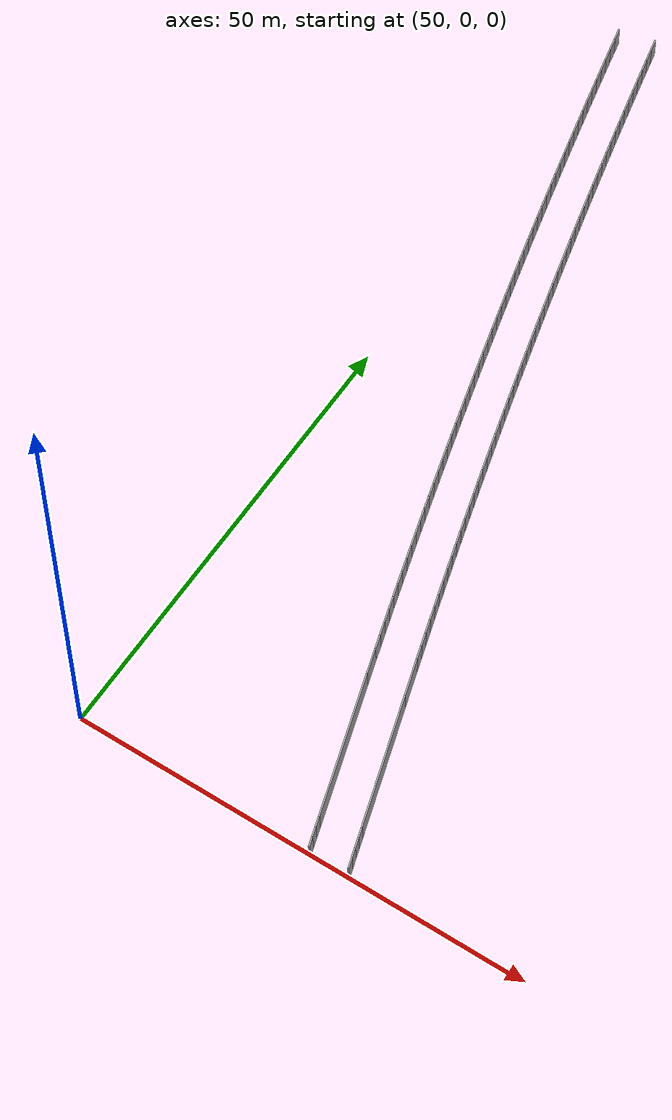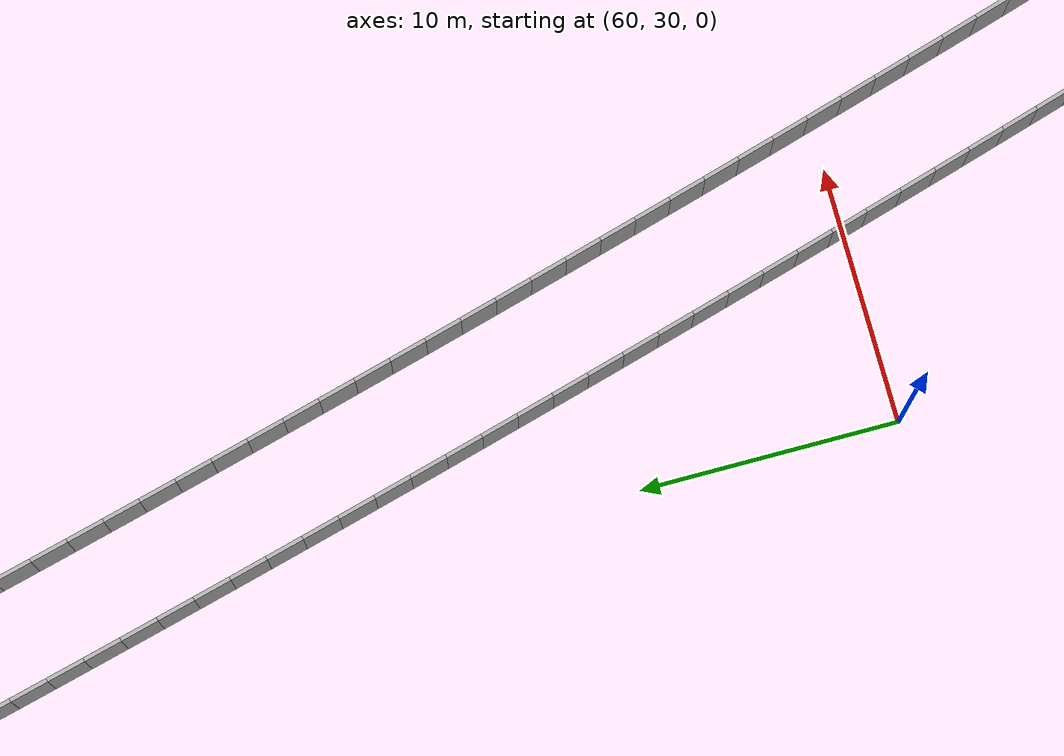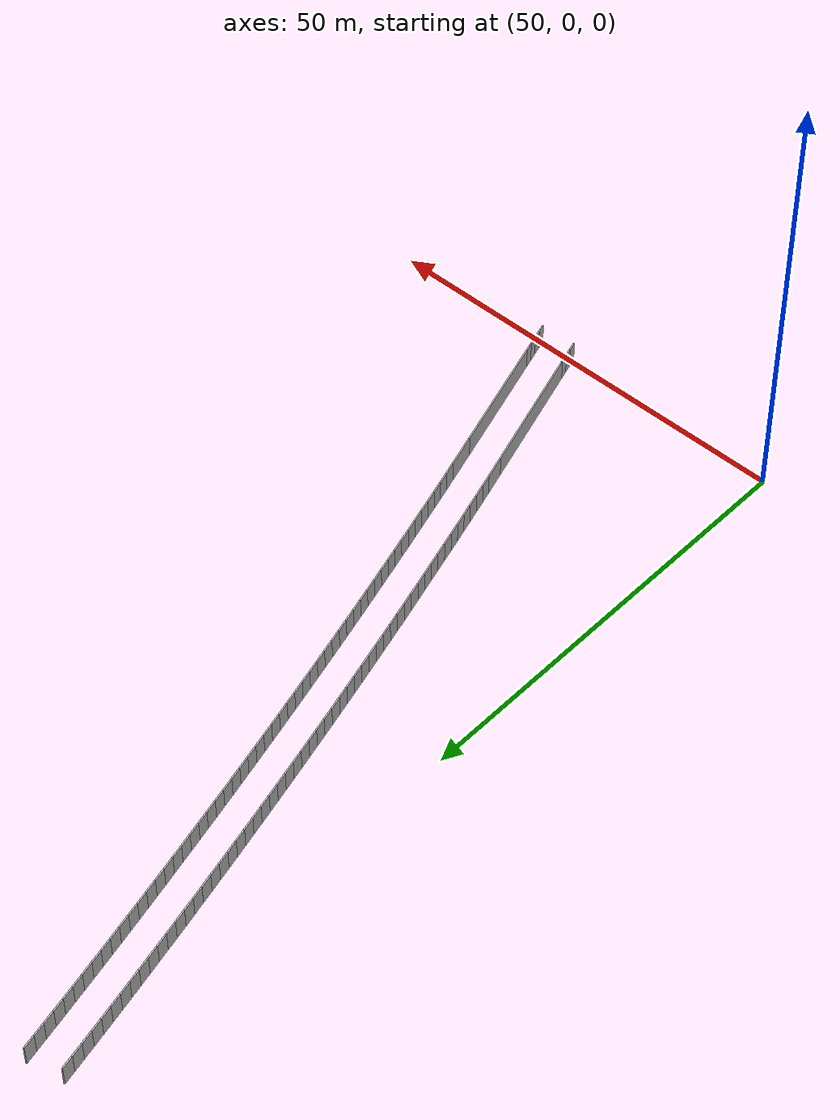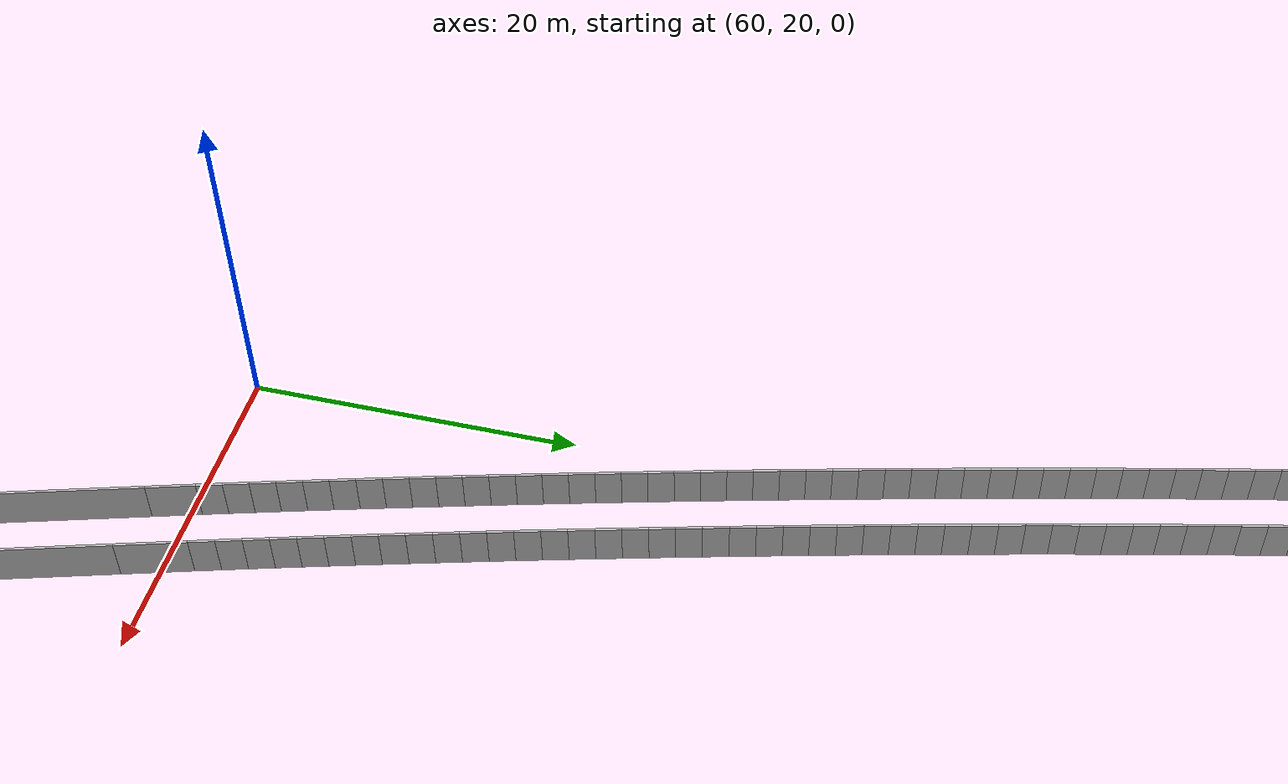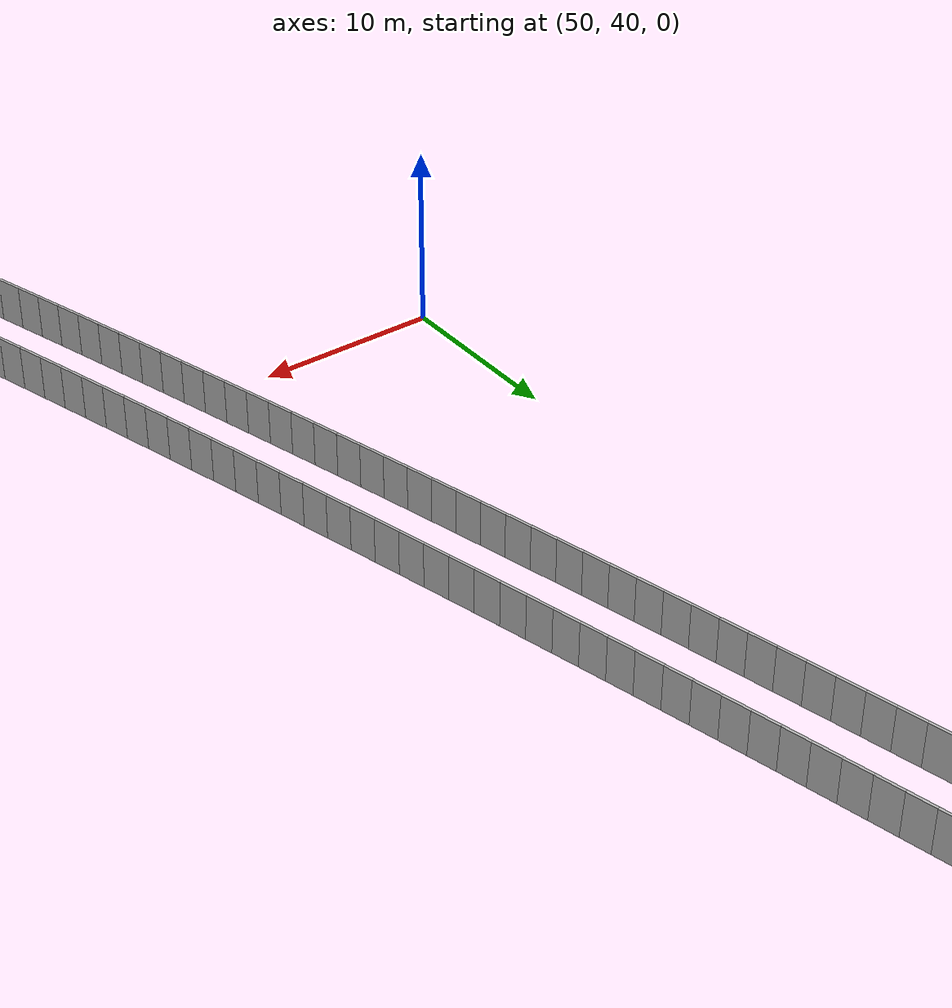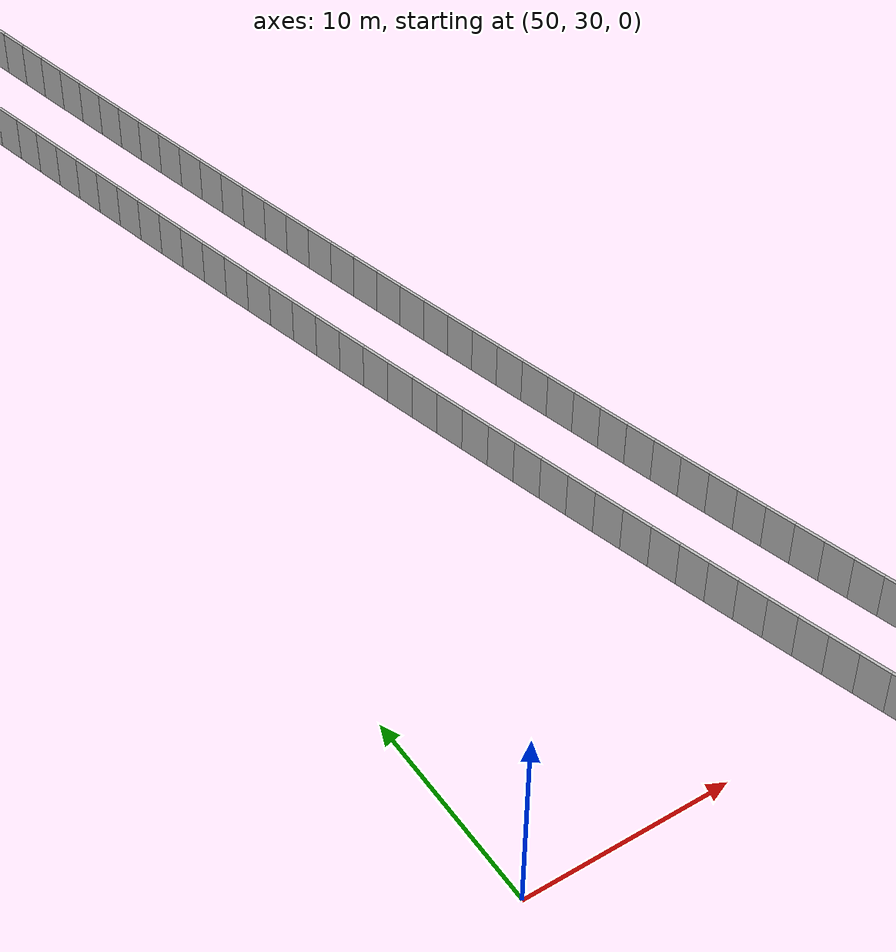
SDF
<?xml version="1.0" ?>
<sdf version="1.6">
  <model name="sps_0110">
    <pose frame="">0 0 0 0 -0 0</pose>
    <static>1</static>
    <self_collide>0</self_collide>
    <allow_auto_disable>0</allow_auto_disable>
    <link name="Wall296">
      <kinematic>0</kinematic>
      <gravity>1</gravity>
      <self_collide>0</self_collide>
      <collision name="collision">
        <geometry>
          <box>
            <size>2.85806 0.15 2.5</size>
          </box>
        </geometry>
        <pose frame="">0 0 0 0 -0 0</pose>
      </collision>
      <visual name="visual">
        <geometry>
          <box>
            <size>2.85806 0.15 2.5</size>
          </box>
        </geometry>
        <pose frame="">0 0 0 0 -0 0</pose>
        <cast_shadows>1</cast_shadows>
        <transparency>0.0</transparency>
      </visual>
      <pose frame="">70.5429 19.2606 1.25 0 0 -1.27627</pose>
    </link>
    <link name="Wall297">
      <kinematic>0</kinematic>
      <gravity>1</gravity>
      <self_collide>0</self_collide>
      <collision name="collision">
        <geometry>
          <box>
            <size>15.8238 0.15 2.5</size>
          </box>
        </geometry>
        <pose frame="">0 0 0 0 -0 0</pose>
      </collision>
      <visual name="visual">
        <geometry>
          <box>
            <size>15.8238 0.15 2.5</size>
          </box>
        </geometry>
        <pose frame="">0 0 0 0 -0 0</pose>
        <cast_shadows>1</cast_shadows>
        <transparency>0.0</transparency>
      </visual>
      <pose frame="">73.2545 10.3219 1.25 0 0 -1.27627</pose>
    </link>
    <link name="Wall366">
      <kinematic>0</kinematic>
      <gravity>1</gravity>
      <self_collide>0</self_collide>
      <collision name="collision">
        <geometry>
          <box>
            <size>14.5713 0.15 2.5</size>
          </box>
        </geometry>
        <pose frame="">0 0 0 0 -0 0</pose>
      </collision>
      <visual name="visual">
        <geometry>
          <box>
            <size>14.5713 0.15 2.5</size>
          </box>
        </geometry>
        <pose frame="">0 0 0 0 -0 0</pose>
        <cast_shadows>1</cast_shadows>
        <transparency>0.0</transparency>
      </visual>
      <pose frame="">77.3989 10.9213 1.25 0 -0 1.86538</pose>
    </link>
    <link name="Wall367">
      <kinematic>0</kinematic>
      <gravity>1</gravity>
      <self_collide>0</self_collide>
      <collision name="collision">
        <geometry>
          <box>
            <size>4.09938 0.15 2.5</size>
          </box>
        </geometry>
        <pose frame="">0 0 0 0 -0 0</pose>
      </collision>
      <visual name="visual">
        <geometry>
          <box>
            <size>4.09938 0.15 2.5</size>
          </box>
        </geometry>
        <pose frame="">0 0 0 0 -0 0</pose>
        <cast_shadows>1</cast_shadows>
        <transparency>0.0</transparency>
      </visual>
      <pose frame="">74.6884 19.8545 1.25 0 -0 1.86538</pose>
    </link>
    <link name="Wall2779">
      <kinematic>0</kinematic>
      <gravity>1</gravity>
      <self_collide>0</self_collide>
      <collision name="collision">
        <geometry>
          <box>
            <size>1.07596 0.15 2.5</size>
          </box>
        </geometry>
        <pose frame="">0 0 0 0 -0 0</pose>
      </collision>
      <visual name="visual">
        <geometry>
          <box>
            <size>1.07596 0.15 2.5</size>
          </box>
        </geometry>
        <pose frame="">0 0 0 0 -0 0</pose>
        <cast_shadows>1</cast_shadows>
        <transparency>0.0</transparency>
      </visual>
      <pose frame="">79.6702 3.43458 1.25 0 0 -1.27676</pose>
    </link>
    <link name="Wall2780">
      <kinematic>0</kinematic>
      <gravity>1</gravity>
      <self_collide>0</self_collide>
      <collision name="collision">
        <geometry>
          <box>
            <size>1.07595 0.15 2.5</size>
          </box>
        </geometry>
        <pose frame="">0 0 0 0 -0 0</pose>
      </collision>
      <visual name="visual">
        <geometry>
          <box>
            <size>1.07595 0.15 2.5</size>
          </box>
        </geometry>
        <pose frame="">0 0 0 0 -0 0</pose>
        <cast_shadows>1</cast_shadows>
        <transparency>0.0</transparency>
      </visual>
      <pose frame="">79.9826 2.40498 1.25 0 0 -1.27563</pose>
    </link>
    <link name="Wall2781">
      <kinematic>0</kinematic>
      <gravity>1</gravity>
      <self_collide>0</self_collide>
      <collision name="collision">
        <geometry>
          <box>
            <size>1.0759 0.15 2.5</size>
          </box>
        </geometry>
        <pose frame="">0 0 0 0 -0 0</pose>
      </collision>
      <visual name="visual">
        <geometry>
          <box>
            <size>1.0759 0.15 2.5</size>
          </box>
        </geometry>
        <pose frame="">0 0 0 0 -0 0</pose>
        <cast_shadows>1</cast_shadows>
        <transparency>0.0</transparency>
      </visual>
      <pose frame="">80.2962 1.37578 1.25 0 0 -1.27443</pose>
    </link>
    <link name="Wall2782">
      <kinematic>0</kinematic>
      <gravity>1</gravity>
      <self_collide>0</self_collide>
      <collision name="collision">
        <geometry>
          <box>
            <size>1.0759 0.15 2.5</size>
          </box>
        </geometry>
        <pose frame="">0 0 0 0 -0 0</pose>
      </collision>
      <visual name="visual">
        <geometry>
          <box>
            <size>1.0759 0.15 2.5</size>
          </box>
        </geometry>
        <pose frame="">0 0 0 0 -0 0</pose>
        <cast_shadows>1</cast_shadows>
        <transparency>0.0</transparency>
      </visual>
      <pose frame="">80.6111 0.346999 1.25 0 0 -1.27307</pose>
    </link>
    <link name="Wall5378">
      <kinematic>0</kinematic>
      <gravity>1</gravity>
      <self_collide>0</self_collide>
      <collision name="collision">
        <geometry>
          <box>
            <size>1.49645 0.15 2.5</size>
          </box>
        </geometry>
        <pose frame="">0 0 0 0 -0 0</pose>
      </collision>
      <visual name="visual">
        <geometry>
          <box>
            <size>1.49645 0.15 2.5</size>
          </box>
        </geometry>
        <pose frame="">0 0 0 0 -0 0</pose>
        <cast_shadows>1</cast_shadows>
        <transparency>0.0</transparency>
      </visual>
      <pose frame="">54.407 99.3969 1.25 0 0 -1.36471</pose>
    </link>
    <link name="Wall5379">
      <kinematic>0</kinematic>
      <gravity>1</gravity>
      <self_collide>0</self_collide>
      <collision name="collision">
        <geometry>
          <box>
            <size>1.49658 0.15 2.5</size>
          </box>
        </geometry>
        <pose frame="">0 0 0 0 -0 0</pose>
      </collision>
      <visual name="visual">
        <geometry>
          <box>
            <size>1.49658 0.15 2.5</size>
          </box>
        </geometry>
        <pose frame="">0 0 0 0 -0 0</pose>
        <cast_shadows>1</cast_shadows>
        <transparency>0.0</transparency>
      </visual>
      <pose frame="">54.7144 97.9323 1.25 0 0 -1.36311</pose>
    </link>
    <link name="Wall5380">
      <kinematic>0</kinematic>
      <gravity>1</gravity>
      <self_collide>0</self_collide>
      <collision name="collision">
        <geometry>
          <box>
            <size>1.49647 0.15 2.5</size>
          </box>
        </geometry>
        <pose frame="">0 0 0 0 -0 0</pose>
      </collision>
      <visual name="visual">
        <geometry>
          <box>
            <size>1.49647 0.15 2.5</size>
          </box>
        </geometry>
        <pose frame="">0 0 0 0 -0 0</pose>
        <cast_shadows>1</cast_shadows>
        <transparency>0.0</transparency>
      </visual>
      <pose frame="">55.0242 96.4682 1.25 0 0 -1.36147</pose>
    </link>
    <link name="Wall5381">
      <kinematic>0</kinematic>
      <gravity>1</gravity>
      <self_collide>0</self_collide>
      <collision name="collision">
        <geometry>
          <box>
            <size>1.49653 0.15 2.5</size>
          </box>
        </geometry>
        <pose frame="">0 0 0 0 -0 0</pose>
      </collision>
      <visual name="visual">
        <geometry>
          <box>
            <size>1.49653 0.15 2.5</size>
          </box>
        </geometry>
        <pose frame="">0 0 0 0 -0 0</pose>
        <cast_shadows>1</cast_shadows>
        <transparency>0.0</transparency>
      </visual>
      <pose frame="">55.3363 95.0046 1.25 0 0 -1.35993</pose>
    </link>
    <link name="Wall5382">
      <kinematic>0</kinematic>
      <gravity>1</gravity>
      <self_collide>0</self_collide>
      <collision name="collision">
        <geometry>
          <box>
            <size>1.49648 0.15 2.5</size>
          </box>
        </geometry>
        <pose frame="">0 0 0 0 -0 0</pose>
      </collision>
      <visual name="visual">
        <geometry>
          <box>
            <size>1.49648 0.15 2.5</size>
          </box>
        </geometry>
        <pose frame="">0 0 0 0 -0 0</pose>
        <cast_shadows>1</cast_shadows>
        <transparency>0.0</transparency>
      </visual>
      <pose frame="">55.6507 93.5415 1.25 0 0 -1.35834</pose>
    </link>
    <link name="Wall5383">
      <kinematic>0</kinematic>
      <gravity>1</gravity>
      <self_collide>0</self_collide>
      <collision name="collision">
        <geometry>
          <box>
            <size>1.49654 0.15 2.5</size>
          </box>
        </geometry>
        <pose frame="">0 0 0 0 -0 0</pose>
      </collision>
      <visual name="visual">
        <geometry>
          <box>
            <size>1.49654 0.15 2.5</size>
          </box>
        </geometry>
        <pose frame="">0 0 0 0 -0 0</pose>
        <cast_shadows>1</cast_shadows>
        <transparency>0.0</transparency>
      </visual>
      <pose frame="">55.9673 92.0789 1.25 0 0 -1.3568</pose>
    </link>
    <link name="Wall5384">
      <kinematic>0</kinematic>
      <gravity>1</gravity>
      <self_collide>0</self_collide>
      <collision name="collision">
        <geometry>
          <box>
            <size>1.49645 0.15 2.5</size>
          </box>
        </geometry>
        <pose frame="">0 0 0 0 -0 0</pose>
      </collision>
      <visual name="visual">
        <geometry>
          <box>
            <size>1.49645 0.15 2.5</size>
          </box>
        </geometry>
        <pose frame="">0 0 0 0 -0 0</pose>
        <cast_shadows>1</cast_shadows>
        <transparency>0.0</transparency>
      </visual>
      <pose frame="">56.2863 90.6168 1.25 0 0 -1.35516</pose>
    </link>
    <link name="Wall5385">
      <kinematic>0</kinematic>
      <gravity>1</gravity>
      <self_collide>0</self_collide>
      <collision name="collision">
        <geometry>
          <box>
            <size>1.49638 0.15 2.5</size>
          </box>
        </geometry>
        <pose frame="">0 0 0 0 -0 0</pose>
      </collision>
      <visual name="visual">
        <geometry>
          <box>
            <size>1.49638 0.15 2.5</size>
          </box>
        </geometry>
        <pose frame="">0 0 0 0 -0 0</pose>
        <cast_shadows>1</cast_shadows>
        <transparency>0.0</transparency>
      </visual>
      <pose frame="">56.6077 89.1553 1.25 0 0 -1.35348</pose>
    </link>
    <link name="Wall5386">
      <kinematic>0</kinematic>
      <gravity>1</gravity>
      <self_collide>0</self_collide>
      <collision name="collision">
        <geometry>
          <box>
            <size>1.49648 0.15 2.5</size>
          </box>
        </geometry>
        <pose frame="">0 0 0 0 -0 0</pose>
      </collision>
      <visual name="visual">
        <geometry>
          <box>
            <size>1.49648 0.15 2.5</size>
          </box>
        </geometry>
        <pose frame="">0 0 0 0 -0 0</pose>
        <cast_shadows>1</cast_shadows>
        <transparency>0.0</transparency>
      </visual>
      <pose frame="">56.9314 87.6943 1.25 0 0 -1.35203</pose>
    </link>
    <link name="Wall5387">
      <kinematic>0</kinematic>
      <gravity>1</gravity>
      <self_collide>0</self_collide>
      <collision name="collision">
        <geometry>
          <box>
            <size>1.4966 0.15 2.5</size>
          </box>
        </geometry>
        <pose frame="">0 0 0 0 -0 0</pose>
      </collision>
      <visual name="visual">
        <geometry>
          <box>
            <size>1.4966 0.15 2.5</size>
          </box>
        </geometry>
        <pose frame="">0 0 0 0 -0 0</pose>
        <cast_shadows>1</cast_shadows>
        <transparency>0.0</transparency>
      </visual>
      <pose frame="">57.2574 86.2337 1.25 0 0 -1.35038</pose>
    </link>
    <link name="Wall5388">
      <kinematic>0</kinematic>
      <gravity>1</gravity>
      <self_collide>0</self_collide>
      <collision name="collision">
        <geometry>
          <box>
            <size>1.49648 0.15 2.5</size>
          </box>
        </geometry>
        <pose frame="">0 0 0 0 -0 0</pose>
      </collision>
      <visual name="visual">
        <geometry>
          <box>
            <size>1.49648 0.15 2.5</size>
          </box>
        </geometry>
        <pose frame="">0 0 0 0 -0 0</pose>
        <cast_shadows>1</cast_shadows>
        <transparency>0.0</transparency>
      </visual>
      <pose frame="">57.5857 84.7736 1.25 0 0 -1.34886</pose>
    </link>
    <link name="Wall5389">
      <kinematic>0</kinematic>
      <gravity>1</gravity>
      <self_collide>0</self_collide>
      <collision name="collision">
        <geometry>
          <box>
            <size>1.49665 0.15 2.5</size>
          </box>
        </geometry>
        <pose frame="">0 0 0 0 -0 0</pose>
      </collision>
      <visual name="visual">
        <geometry>
          <box>
            <size>1.49665 0.15 2.5</size>
          </box>
        </geometry>
        <pose frame="">0 0 0 0 -0 0</pose>
        <cast_shadows>1</cast_shadows>
        <transparency>0.0</transparency>
      </visual>
      <pose frame="">57.9163 83.314 1.25 0 0 -1.34725</pose>
    </link>
    <link name="Wall5390">
      <kinematic>0</kinematic>
      <gravity>1</gravity>
      <self_collide>0</self_collide>
      <collision name="collision">
        <geometry>
          <box>
            <size>1.49638 0.15 2.5</size>
          </box>
        </geometry>
        <pose frame="">0 0 0 0 -0 0</pose>
      </collision>
      <visual name="visual">
        <geometry>
          <box>
            <size>1.49638 0.15 2.5</size>
          </box>
        </geometry>
        <pose frame="">0 0 0 0 -0 0</pose>
        <cast_shadows>1</cast_shadows>
        <transparency>0.0</transparency>
      </visual>
      <pose frame="">58.2493 81.855 1.25 0 0 -1.34566</pose>
    </link>
    <link name="Wall5391">
      <kinematic>0</kinematic>
      <gravity>1</gravity>
      <self_collide>0</self_collide>
      <collision name="collision">
        <geometry>
          <box>
            <size>1.49648 0.15 2.5</size>
          </box>
        </geometry>
        <pose frame="">0 0 0 0 -0 0</pose>
      </collision>
      <visual name="visual">
        <geometry>
          <box>
            <size>1.49648 0.15 2.5</size>
          </box>
        </geometry>
        <pose frame="">0 0 0 0 -0 0</pose>
        <cast_shadows>1</cast_shadows>
        <transparency>0.0</transparency>
      </visual>
      <pose frame="">58.5845 80.3966 1.25 0 0 -1.34409</pose>
    </link>
    <link name="Wall5392">
      <kinematic>0</kinematic>
      <gravity>1</gravity>
      <self_collide>0</self_collide>
      <collision name="collision">
        <geometry>
          <box>
            <size>1.49668 0.15 2.5</size>
          </box>
        </geometry>
        <pose frame="">0 0 0 0 -0 0</pose>
      </collision>
      <visual name="visual">
        <geometry>
          <box>
            <size>1.49668 0.15 2.5</size>
          </box>
        </geometry>
        <pose frame="">0 0 0 0 -0 0</pose>
        <cast_shadows>1</cast_shadows>
        <transparency>0.0</transparency>
      </visual>
      <pose frame="">58.922 78.9386 1.25 0 0 -1.34244</pose>
    </link>
    <link name="Wall5393">
      <kinematic>0</kinematic>
      <gravity>1</gravity>
      <self_collide>0</self_collide>
      <collision name="collision">
        <geometry>
          <box>
            <size>1.49652 0.15 2.5</size>
          </box>
        </geometry>
        <pose frame="">0 0 0 0 -0 0</pose>
      </collision>
      <visual name="visual">
        <geometry>
          <box>
            <size>1.49652 0.15 2.5</size>
          </box>
        </geometry>
        <pose frame="">0 0 0 0 -0 0</pose>
        <cast_shadows>1</cast_shadows>
        <transparency>0.0</transparency>
      </visual>
      <pose frame="">59.262 77.4811 1.25 0 0 -1.34091</pose>
    </link>
    <link name="Wall5394">
      <kinematic>0</kinematic>
      <gravity>1</gravity>
      <self_collide>0</self_collide>
      <collision name="collision">
        <geometry>
          <box>
            <size>1.49653 0.15 2.5</size>
          </box>
        </geometry>
        <pose frame="">0 0 0 0 -0 0</pose>
      </collision>
      <visual name="visual">
        <geometry>
          <box>
            <size>1.49653 0.15 2.5</size>
          </box>
        </geometry>
        <pose frame="">0 0 0 0 -0 0</pose>
        <cast_shadows>1</cast_shadows>
        <transparency>0.0</transparency>
      </visual>
      <pose frame="">59.6041 76.0242 1.25 0 0 -1.33928</pose>
    </link>
    <link name="Wall5395">
      <kinematic>0</kinematic>
      <gravity>1</gravity>
      <self_collide>0</self_collide>
      <collision name="collision">
        <geometry>
          <box>
            <size>1.49646 0.15 2.5</size>
          </box>
        </geometry>
        <pose frame="">0 0 0 0 -0 0</pose>
      </collision>
      <visual name="visual">
        <geometry>
          <box>
            <size>1.49646 0.15 2.5</size>
          </box>
        </geometry>
        <pose frame="">0 0 0 0 -0 0</pose>
        <cast_shadows>1</cast_shadows>
        <transparency>0.0</transparency>
      </visual>
      <pose frame="">59.9487 74.5679 1.25 0 0 -1.33772</pose>
    </link>
    <link name="Wall5396">
      <kinematic>0</kinematic>
      <gravity>1</gravity>
      <self_collide>0</self_collide>
      <collision name="collision">
        <geometry>
          <box>
            <size>1.49646 0.15 2.5</size>
          </box>
        </geometry>
        <pose frame="">0 0 0 0 -0 0</pose>
      </collision>
      <visual name="visual">
        <geometry>
          <box>
            <size>1.49646 0.15 2.5</size>
          </box>
        </geometry>
        <pose frame="">0 0 0 0 -0 0</pose>
        <cast_shadows>1</cast_shadows>
        <transparency>0.0</transparency>
      </visual>
      <pose frame="">60.2955 73.1122 1.25 0 0 -1.33613</pose>
    </link>
    <link name="Wall5397">
      <kinematic>0</kinematic>
      <gravity>1</gravity>
      <self_collide>0</self_collide>
      <collision name="collision">
        <geometry>
          <box>
            <size>1.49651 0.15 2.5</size>
          </box>
        </geometry>
        <pose frame="">0 0 0 0 -0 0</pose>
      </collision>
      <visual name="visual">
        <geometry>
          <box>
            <size>1.49651 0.15 2.5</size>
          </box>
        </geometry>
        <pose frame="">0 0 0 0 -0 0</pose>
        <cast_shadows>1</cast_shadows>
        <transparency>0.0</transparency>
      </visual>
      <pose frame="">60.6446 71.657 1.25 0 0 -1.33458</pose>
    </link>
    <link name="Wall5398">
      <kinematic>0</kinematic>
      <gravity>1</gravity>
      <self_collide>0</self_collide>
      <collision name="collision">
        <geometry>
          <box>
            <size>1.49654 0.15 2.5</size>
          </box>
        </geometry>
        <pose frame="">0 0 0 0 -0 0</pose>
      </collision>
      <visual name="visual">
        <geometry>
          <box>
            <size>1.49654 0.15 2.5</size>
          </box>
        </geometry>
        <pose frame="">0 0 0 0 -0 0</pose>
        <cast_shadows>1</cast_shadows>
        <transparency>0.0</transparency>
      </visual>
      <pose frame="">60.996 70.2023 1.25 0 0 -1.33295</pose>
    </link>
    <link name="Wall5399">
      <kinematic>0</kinematic>
      <gravity>1</gravity>
      <self_collide>0</self_collide>
      <collision name="collision">
        <geometry>
          <box>
            <size>1.4967 0.15 2.5</size>
          </box>
        </geometry>
        <pose frame="">0 0 0 0 -0 0</pose>
      </collision>
      <visual name="visual">
        <geometry>
          <box>
            <size>1.4967 0.15 2.5</size>
          </box>
        </geometry>
        <pose frame="">0 0 0 0 -0 0</pose>
        <cast_shadows>1</cast_shadows>
        <transparency>0.0</transparency>
      </visual>
      <pose frame="">61.3497 68.7481 1.25 0 0 -1.33147</pose>
    </link>
    <link name="Wall5400">
      <kinematic>0</kinematic>
      <gravity>1</gravity>
      <self_collide>0</self_collide>
      <collision name="collision">
        <geometry>
          <box>
            <size>1.49644 0.15 2.5</size>
          </box>
        </geometry>
        <pose frame="">0 0 0 0 -0 0</pose>
      </collision>
      <visual name="visual">
        <geometry>
          <box>
            <size>1.49644 0.15 2.5</size>
          </box>
        </geometry>
        <pose frame="">0 0 0 0 -0 0</pose>
        <cast_shadows>1</cast_shadows>
        <transparency>0.0</transparency>
      </visual>
      <pose frame="">61.7056 67.2945 1.25 0 0 -1.32978</pose>
    </link>
    <link name="Wall5401">
      <kinematic>0</kinematic>
      <gravity>1</gravity>
      <self_collide>0</self_collide>
      <collision name="collision">
        <geometry>
          <box>
            <size>1.49639 0.15 2.5</size>
          </box>
        </geometry>
        <pose frame="">0 0 0 0 -0 0</pose>
      </collision>
      <visual name="visual">
        <geometry>
          <box>
            <size>1.49639 0.15 2.5</size>
          </box>
        </geometry>
        <pose frame="">0 0 0 0 -0 0</pose>
        <cast_shadows>1</cast_shadows>
        <transparency>0.0</transparency>
      </visual>
      <pose frame="">62.064 65.8416 1.25 0 0 -1.32822</pose>
    </link>
    <link name="Wall5402">
      <kinematic>0</kinematic>
      <gravity>1</gravity>
      <self_collide>0</self_collide>
      <collision name="collision">
        <geometry>
          <box>
            <size>1.49659 0.15 2.5</size>
          </box>
        </geometry>
        <pose frame="">0 0 0 0 -0 0</pose>
      </collision>
      <visual name="visual">
        <geometry>
          <box>
            <size>1.49659 0.15 2.5</size>
          </box>
        </geometry>
        <pose frame="">0 0 0 0 -0 0</pose>
        <cast_shadows>1</cast_shadows>
        <transparency>0.0</transparency>
      </visual>
      <pose frame="">62.4246 64.3892 1.25 0 0 -1.32666</pose>
    </link>
    <link name="Wall5403">
      <kinematic>0</kinematic>
      <gravity>1</gravity>
      <self_collide>0</self_collide>
      <collision name="collision">
        <geometry>
          <box>
            <size>1.49654 0.15 2.5</size>
          </box>
        </geometry>
        <pose frame="">0 0 0 0 -0 0</pose>
      </collision>
      <visual name="visual">
        <geometry>
          <box>
            <size>1.49654 0.15 2.5</size>
          </box>
        </geometry>
        <pose frame="">0 0 0 0 -0 0</pose>
        <cast_shadows>1</cast_shadows>
        <transparency>0.0</transparency>
      </visual>
      <pose frame="">62.7874 62.9373 1.25 0 0 -1.3251</pose>
    </link>
    <link name="Wall5404">
      <kinematic>0</kinematic>
      <gravity>1</gravity>
      <self_collide>0</self_collide>
      <collision name="collision">
        <geometry>
          <box>
            <size>1.49653 0.15 2.5</size>
          </box>
        </geometry>
        <pose frame="">0 0 0 0 -0 0</pose>
      </collision>
      <visual name="visual">
        <geometry>
          <box>
            <size>1.49653 0.15 2.5</size>
          </box>
        </geometry>
        <pose frame="">0 0 0 0 -0 0</pose>
        <cast_shadows>1</cast_shadows>
        <transparency>0.0</transparency>
      </visual>
      <pose frame="">63.1526 61.486 1.25 0 0 -1.32345</pose>
    </link>
    <link name="Wall5405">
      <kinematic>0</kinematic>
      <gravity>1</gravity>
      <self_collide>0</self_collide>
      <collision name="collision">
        <geometry>
          <box>
            <size>1.49654 0.15 2.5</size>
          </box>
        </geometry>
        <pose frame="">0 0 0 0 -0 0</pose>
      </collision>
      <visual name="visual">
        <geometry>
          <box>
            <size>1.49654 0.15 2.5</size>
          </box>
        </geometry>
        <pose frame="">0 0 0 0 -0 0</pose>
        <cast_shadows>1</cast_shadows>
        <transparency>0.0</transparency>
      </visual>
      <pose frame="">63.5201 60.0353 1.25 0 0 -1.32194</pose>
    </link>
    <link name="Wall5406">
      <kinematic>0</kinematic>
      <gravity>1</gravity>
      <self_collide>0</self_collide>
      <collision name="collision">
        <geometry>
          <box>
            <size>1.49649 0.15 2.5</size>
          </box>
        </geometry>
        <pose frame="">0 0 0 0 -0 0</pose>
      </collision>
      <visual name="visual">
        <geometry>
          <box>
            <size>1.49649 0.15 2.5</size>
          </box>
        </geometry>
        <pose frame="">0 0 0 0 -0 0</pose>
        <cast_shadows>1</cast_shadows>
        <transparency>0.0</transparency>
      </visual>
      <pose frame="">63.8899 58.5852 1.25 0 0 -1.32025</pose>
    </link>
    <link name="Wall5407">
      <kinematic>0</kinematic>
      <gravity>1</gravity>
      <self_collide>0</self_collide>
      <collision name="collision">
        <geometry>
          <box>
            <size>1.49649 0.15 2.5</size>
          </box>
        </geometry>
        <pose frame="">0 0 0 0 -0 0</pose>
      </collision>
      <visual name="visual">
        <geometry>
          <box>
            <size>1.49649 0.15 2.5</size>
          </box>
        </geometry>
        <pose frame="">0 0 0 0 -0 0</pose>
        <cast_shadows>1</cast_shadows>
        <transparency>0.0</transparency>
      </visual>
      <pose frame="">64.262 57.1357 1.25 0 0 -1.31877</pose>
    </link>
    <link name="Wall5408">
      <kinematic>0</kinematic>
      <gravity>1</gravity>
      <self_collide>0</self_collide>
      <collision name="collision">
        <geometry>
          <box>
            <size>1.49651 0.15 2.5</size>
          </box>
        </geometry>
        <pose frame="">0 0 0 0 -0 0</pose>
      </collision>
      <visual name="visual">
        <geometry>
          <box>
            <size>1.49651 0.15 2.5</size>
          </box>
        </geometry>
        <pose frame="">0 0 0 0 -0 0</pose>
        <cast_shadows>1</cast_shadows>
        <transparency>0.0</transparency>
      </visual>
      <pose frame="">64.6364 55.6868 1.25 0 0 -1.31709</pose>
    </link>
    <link name="Wall5409">
      <kinematic>0</kinematic>
      <gravity>1</gravity>
      <self_collide>0</self_collide>
      <collision name="collision">
        <geometry>
          <box>
            <size>1.49647 0.15 2.5</size>
          </box>
        </geometry>
        <pose frame="">0 0 0 0 -0 0</pose>
      </collision>
      <visual name="visual">
        <geometry>
          <box>
            <size>1.49647 0.15 2.5</size>
          </box>
        </geometry>
        <pose frame="">0 0 0 0 -0 0</pose>
        <cast_shadows>1</cast_shadows>
        <transparency>0.0</transparency>
      </visual>
      <pose frame="">65.0131 54.2385 1.25 0 0 -1.31557</pose>
    </link>
    <link name="Wall5410">
      <kinematic>0</kinematic>
      <gravity>1</gravity>
      <self_collide>0</self_collide>
      <collision name="collision">
        <geometry>
          <box>
            <size>1.49649 0.15 2.5</size>
          </box>
        </geometry>
        <pose frame="">0 0 0 0 -0 0</pose>
      </collision>
      <visual name="visual">
        <geometry>
          <box>
            <size>1.49649 0.15 2.5</size>
          </box>
        </geometry>
        <pose frame="">0 0 0 0 -0 0</pose>
        <cast_shadows>1</cast_shadows>
        <transparency>0.0</transparency>
      </visual>
      <pose frame="">65.3921 52.7908 1.25 0 0 -1.31393</pose>
    </link>
    <link name="Wall5411">
      <kinematic>0</kinematic>
      <gravity>1</gravity>
      <self_collide>0</self_collide>
      <collision name="collision">
        <geometry>
          <box>
            <size>1.49647 0.15 2.5</size>
          </box>
        </geometry>
        <pose frame="">0 0 0 0 -0 0</pose>
      </collision>
      <visual name="visual">
        <geometry>
          <box>
            <size>1.49647 0.15 2.5</size>
          </box>
        </geometry>
        <pose frame="">0 0 0 0 -0 0</pose>
        <cast_shadows>1</cast_shadows>
        <transparency>0.0</transparency>
      </visual>
      <pose frame="">65.7735 51.3437 1.25 0 0 -1.31236</pose>
    </link>
    <link name="Wall5412">
      <kinematic>0</kinematic>
      <gravity>1</gravity>
      <self_collide>0</self_collide>
      <collision name="collision">
        <geometry>
          <box>
            <size>1.49649 0.15 2.5</size>
          </box>
        </geometry>
        <pose frame="">0 0 0 0 -0 0</pose>
      </collision>
      <visual name="visual">
        <geometry>
          <box>
            <size>1.49649 0.15 2.5</size>
          </box>
        </geometry>
        <pose frame="">0 0 0 0 -0 0</pose>
        <cast_shadows>1</cast_shadows>
        <transparency>0.0</transparency>
      </visual>
      <pose frame="">66.157 49.8972 1.25 0 0 -1.31089</pose>
    </link>
    <link name="Wall5413">
      <kinematic>0</kinematic>
      <gravity>1</gravity>
      <self_collide>0</self_collide>
      <collision name="collision">
        <geometry>
          <box>
            <size>1.49651 0.15 2.5</size>
          </box>
        </geometry>
        <pose frame="">0 0 0 0 -0 0</pose>
      </collision>
      <visual name="visual">
        <geometry>
          <box>
            <size>1.49651 0.15 2.5</size>
          </box>
        </geometry>
        <pose frame="">0 0 0 0 -0 0</pose>
        <cast_shadows>1</cast_shadows>
        <transparency>0.0</transparency>
      </visual>
      <pose frame="">66.5427 48.4513 1.25 0 0 -1.30925</pose>
    </link>
    <link name="Wall5414">
      <kinematic>0</kinematic>
      <gravity>1</gravity>
      <self_collide>0</self_collide>
      <collision name="collision">
        <geometry>
          <box>
            <size>1.4965 0.15 2.5</size>
          </box>
        </geometry>
        <pose frame="">0 0 0 0 -0 0</pose>
      </collision>
      <visual name="visual">
        <geometry>
          <box>
            <size>1.4965 0.15 2.5</size>
          </box>
        </geometry>
        <pose frame="">0 0 0 0 -0 0</pose>
        <cast_shadows>1</cast_shadows>
        <transparency>0.0</transparency>
      </visual>
      <pose frame="">66.9309 47.006 1.25 0 0 -1.30756</pose>
    </link>
    <link name="Wall5415">
      <kinematic>0</kinematic>
      <gravity>1</gravity>
      <self_collide>0</self_collide>
      <collision name="collision">
        <geometry>
          <box>
            <size>1.49678 0.15 2.5</size>
          </box>
        </geometry>
        <pose frame="">0 0 0 0 -0 0</pose>
      </collision>
      <visual name="visual">
        <geometry>
          <box>
            <size>1.49678 0.15 2.5</size>
          </box>
        </geometry>
        <pose frame="">0 0 0 0 -0 0</pose>
        <cast_shadows>1</cast_shadows>
        <transparency>0.0</transparency>
      </visual>
      <pose frame="">67.3214 45.5612 1.25 0 0 -1.30609</pose>
    </link>
    <link name="Wall5416">
      <kinematic>0</kinematic>
      <gravity>1</gravity>
      <self_collide>0</self_collide>
      <collision name="collision">
        <geometry>
          <box>
            <size>1.49635 0.15 2.5</size>
          </box>
        </geometry>
        <pose frame="">0 0 0 0 -0 0</pose>
      </collision>
      <visual name="visual">
        <geometry>
          <box>
            <size>1.49635 0.15 2.5</size>
          </box>
        </geometry>
        <pose frame="">0 0 0 0 -0 0</pose>
        <cast_shadows>1</cast_shadows>
        <transparency>0.0</transparency>
      </visual>
      <pose frame="">67.7141 44.1171 1.25 0 0 -1.30449</pose>
    </link>
    <link name="Wall5417">
      <kinematic>0</kinematic>
      <gravity>1</gravity>
      <self_collide>0</self_collide>
      <collision name="collision">
        <geometry>
          <box>
            <size>1.49658 0.15 2.5</size>
          </box>
        </geometry>
        <pose frame="">0 0 0 0 -0 0</pose>
      </collision>
      <visual name="visual">
        <geometry>
          <box>
            <size>1.49658 0.15 2.5</size>
          </box>
        </geometry>
        <pose frame="">0 0 0 0 -0 0</pose>
        <cast_shadows>1</cast_shadows>
        <transparency>0.0</transparency>
      </visual>
      <pose frame="">68.1092 42.6737 1.25 0 0 -1.30284</pose>
    </link>
    <link name="Wall5418">
      <kinematic>0</kinematic>
      <gravity>1</gravity>
      <self_collide>0</self_collide>
      <collision name="collision">
        <geometry>
          <box>
            <size>1.49667 0.15 2.5</size>
          </box>
        </geometry>
        <pose frame="">0 0 0 0 -0 0</pose>
      </collision>
      <visual name="visual">
        <geometry>
          <box>
            <size>1.49667 0.15 2.5</size>
          </box>
        </geometry>
        <pose frame="">0 0 0 0 -0 0</pose>
        <cast_shadows>1</cast_shadows>
        <transparency>0.0</transparency>
      </visual>
      <pose frame="">68.5066 41.2308 1.25 0 0 -1.30125</pose>
    </link>
    <link name="Wall5419">
      <kinematic>0</kinematic>
      <gravity>1</gravity>
      <self_collide>0</self_collide>
      <collision name="collision">
        <geometry>
          <box>
            <size>1.49645 0.15 2.5</size>
          </box>
        </geometry>
        <pose frame="">0 0 0 0 -0 0</pose>
      </collision>
      <visual name="visual">
        <geometry>
          <box>
            <size>1.49645 0.15 2.5</size>
          </box>
        </geometry>
        <pose frame="">0 0 0 0 -0 0</pose>
        <cast_shadows>1</cast_shadows>
        <transparency>0.0</transparency>
      </visual>
      <pose frame="">68.9062 39.7886 1.25 0 0 -1.29964</pose>
    </link>
    <link name="Wall5420">
      <kinematic>0</kinematic>
      <gravity>1</gravity>
      <self_collide>0</self_collide>
      <collision name="collision">
        <geometry>
          <box>
            <size>1.49646 0.15 2.5</size>
          </box>
        </geometry>
        <pose frame="">0 0 0 0 -0 0</pose>
      </collision>
      <visual name="visual">
        <geometry>
          <box>
            <size>1.49646 0.15 2.5</size>
          </box>
        </geometry>
        <pose frame="">0 0 0 0 -0 0</pose>
        <cast_shadows>1</cast_shadows>
        <transparency>0.0</transparency>
      </visual>
      <pose frame="">69.3081 38.3471 1.25 0 0 -1.29824</pose>
    </link>
    <link name="Wall5421">
      <kinematic>0</kinematic>
      <gravity>1</gravity>
      <self_collide>0</self_collide>
      <collision name="collision">
        <geometry>
          <box>
            <size>1.49657 0.15 2.5</size>
          </box>
        </geometry>
        <pose frame="">0 0 0 0 -0 0</pose>
      </collision>
      <visual name="visual">
        <geometry>
          <box>
            <size>1.49657 0.15 2.5</size>
          </box>
        </geometry>
        <pose frame="">0 0 0 0 -0 0</pose>
        <cast_shadows>1</cast_shadows>
        <transparency>0.0</transparency>
      </visual>
      <pose frame="">69.7122 36.9062 1.25 0 0 -1.29649</pose>
    </link>
    <link name="Wall5422">
      <kinematic>0</kinematic>
      <gravity>1</gravity>
      <self_collide>0</self_collide>
      <collision name="collision">
        <geometry>
          <box>
            <size>1.49651 0.15 2.5</size>
          </box>
        </geometry>
        <pose frame="">0 0 0 0 -0 0</pose>
      </collision>
      <visual name="visual">
        <geometry>
          <box>
            <size>1.49651 0.15 2.5</size>
          </box>
        </geometry>
        <pose frame="">0 0 0 0 -0 0</pose>
        <cast_shadows>1</cast_shadows>
        <transparency>0.0</transparency>
      </visual>
      <pose frame="">70.1186 35.4659 1.25 0 0 -1.29512</pose>
    </link>
    <link name="Wall5423">
      <kinematic>0</kinematic>
      <gravity>1</gravity>
      <self_collide>0</self_collide>
      <collision name="collision">
        <geometry>
          <box>
            <size>1.49666 0.15 2.5</size>
          </box>
        </geometry>
        <pose frame="">0 0 0 0 -0 0</pose>
      </collision>
      <visual name="visual">
        <geometry>
          <box>
            <size>1.49666 0.15 2.5</size>
          </box>
        </geometry>
        <pose frame="">0 0 0 0 -0 0</pose>
        <cast_shadows>1</cast_shadows>
        <transparency>0.0</transparency>
      </visual>
      <pose frame="">70.5272 34.0262 1.25 0 0 -1.29328</pose>
    </link>
    <link name="Wall5424">
      <kinematic>0</kinematic>
      <gravity>1</gravity>
      <self_collide>0</self_collide>
      <collision name="collision">
        <geometry>
          <box>
            <size>1.49666 0.15 2.5</size>
          </box>
        </geometry>
        <pose frame="">0 0 0 0 -0 0</pose>
      </collision>
      <visual name="visual">
        <geometry>
          <box>
            <size>1.49666 0.15 2.5</size>
          </box>
        </geometry>
        <pose frame="">0 0 0 0 -0 0</pose>
        <cast_shadows>1</cast_shadows>
        <transparency>0.0</transparency>
      </visual>
      <pose frame="">70.9383 32.5871 1.25 0 0 -1.2918</pose>
    </link>
    <link name="Wall5425">
      <kinematic>0</kinematic>
      <gravity>1</gravity>
      <self_collide>0</self_collide>
      <collision name="collision">
        <geometry>
          <box>
            <size>1.49652 0.15 2.5</size>
          </box>
        </geometry>
        <pose frame="">0 0 0 0 -0 0</pose>
      </collision>
      <visual name="visual">
        <geometry>
          <box>
            <size>1.49652 0.15 2.5</size>
          </box>
        </geometry>
        <pose frame="">0 0 0 0 -0 0</pose>
        <cast_shadows>1</cast_shadows>
        <transparency>0.0</transparency>
      </visual>
      <pose frame="">71.3516 31.1487 1.25 0 0 -1.2902</pose>
    </link>
    <link name="Wall5426">
      <kinematic>0</kinematic>
      <gravity>1</gravity>
      <self_collide>0</self_collide>
      <collision name="collision">
        <geometry>
          <box>
            <size>1.49642 0.15 2.5</size>
          </box>
        </geometry>
        <pose frame="">0 0 0 0 -0 0</pose>
      </collision>
      <visual name="visual">
        <geometry>
          <box>
            <size>1.49642 0.15 2.5</size>
          </box>
        </geometry>
        <pose frame="">0 0 0 0 -0 0</pose>
        <cast_shadows>1</cast_shadows>
        <transparency>0.0</transparency>
      </visual>
      <pose frame="">71.7673 29.7111 1.25 0 0 -1.28852</pose>
    </link>
    <link name="Wall5427">
      <kinematic>0</kinematic>
      <gravity>1</gravity>
      <self_collide>0</self_collide>
      <collision name="collision">
        <geometry>
          <box>
            <size>1.49661 0.15 2.5</size>
          </box>
        </geometry>
        <pose frame="">0 0 0 0 -0 0</pose>
      </collision>
      <visual name="visual">
        <geometry>
          <box>
            <size>1.49661 0.15 2.5</size>
          </box>
        </geometry>
        <pose frame="">0 0 0 0 -0 0</pose>
        <cast_shadows>1</cast_shadows>
        <transparency>0.0</transparency>
      </visual>
      <pose frame="">72.1851 28.2741 1.25 0 0 -1.2872</pose>
    </link>
    <link name="Wall5428">
      <kinematic>0</kinematic>
      <gravity>1</gravity>
      <self_collide>0</self_collide>
      <collision name="collision">
        <geometry>
          <box>
            <size>1.4963 0.15 2.5</size>
          </box>
        </geometry>
        <pose frame="">0 0 0 0 -0 0</pose>
      </collision>
      <visual name="visual">
        <geometry>
          <box>
            <size>1.4963 0.15 2.5</size>
          </box>
        </geometry>
        <pose frame="">0 0 0 0 -0 0</pose>
        <cast_shadows>1</cast_shadows>
        <transparency>0.0</transparency>
      </visual>
      <pose frame="">72.605 26.8378 1.25 0 0 -1.28544</pose>
    </link>
    <link name="Wall5429">
      <kinematic>0</kinematic>
      <gravity>1</gravity>
      <self_collide>0</self_collide>
      <collision name="collision">
        <geometry>
          <box>
            <size>1.49664 0.15 2.5</size>
          </box>
        </geometry>
        <pose frame="">0 0 0 0 -0 0</pose>
      </collision>
      <visual name="visual">
        <geometry>
          <box>
            <size>1.49664 0.15 2.5</size>
          </box>
        </geometry>
        <pose frame="">0 0 0 0 -0 0</pose>
        <cast_shadows>1</cast_shadows>
        <transparency>0.0</transparency>
      </visual>
      <pose frame="">73.0275 25.4022 1.25 0 0 -1.28381</pose>
    </link>
    <link name="Wall5430">
      <kinematic>0</kinematic>
      <gravity>1</gravity>
      <self_collide>0</self_collide>
      <collision name="collision">
        <geometry>
          <box>
            <size>1.49648 0.15 2.5</size>
          </box>
        </geometry>
        <pose frame="">0 0 0 0 -0 0</pose>
      </collision>
      <visual name="visual">
        <geometry>
          <box>
            <size>1.49648 0.15 2.5</size>
          </box>
        </geometry>
        <pose frame="">0 0 0 0 -0 0</pose>
        <cast_shadows>1</cast_shadows>
        <transparency>0.0</transparency>
      </visual>
      <pose frame="">73.4523 23.9672 1.25 0 0 -1.28216</pose>
    </link>
    <link name="Wall5431">
      <kinematic>0</kinematic>
      <gravity>1</gravity>
      <self_collide>0</self_collide>
      <collision name="collision">
        <geometry>
          <box>
            <size>1.49654 0.15 2.5</size>
          </box>
        </geometry>
        <pose frame="">0 0 0 0 -0 0</pose>
      </collision>
      <visual name="visual">
        <geometry>
          <box>
            <size>1.49654 0.15 2.5</size>
          </box>
        </geometry>
        <pose frame="">0 0 0 0 -0 0</pose>
        <cast_shadows>1</cast_shadows>
        <transparency>0.0</transparency>
      </visual>
      <pose frame="">73.8793 22.5329 1.25 0 0 -1.28073</pose>
    </link>
    <link name="Wall7174">
      <kinematic>0</kinematic>
      <gravity>1</gravity>
      <self_collide>0</self_collide>
      <collision name="collision">
        <geometry>
          <box>
            <size>1.50301 0.15 2.5</size>
          </box>
        </geometry>
        <pose frame="">0 0 0 0 -0 0</pose>
      </collision>
      <visual name="visual">
        <geometry>
          <box>
            <size>1.50301 0.15 2.5</size>
          </box>
        </geometry>
        <pose frame="">0 0 0 0 -0 0</pose>
        <cast_shadows>1</cast_shadows>
        <transparency>0.0</transparency>
      </visual>
      <pose frame="">50.3552 98.5493 1.25 0 0 -1.36467</pose>
    </link>
    <link name="Wall7175">
      <kinematic>0</kinematic>
      <gravity>1</gravity>
      <self_collide>0</self_collide>
      <collision name="collision">
        <geometry>
          <box>
            <size>1.50308 0.15 2.5</size>
          </box>
        </geometry>
        <pose frame="">0 0 0 0 -0 0</pose>
      </collision>
      <visual name="visual">
        <geometry>
          <box>
            <size>1.50308 0.15 2.5</size>
          </box>
        </geometry>
        <pose frame="">0 0 0 0 -0 0</pose>
        <cast_shadows>1</cast_shadows>
        <transparency>0.0</transparency>
      </visual>
      <pose frame="">50.6641 97.0783 1.25 0 0 -1.36306</pose>
    </link>
    <link name="Wall7176">
      <kinematic>0</kinematic>
      <gravity>1</gravity>
      <self_collide>0</self_collide>
      <collision name="collision">
        <geometry>
          <box>
            <size>1.50303 0.15 2.5</size>
          </box>
        </geometry>
        <pose frame="">0 0 0 0 -0 0</pose>
      </collision>
      <visual name="visual">
        <geometry>
          <box>
            <size>1.50303 0.15 2.5</size>
          </box>
        </geometry>
        <pose frame="">0 0 0 0 -0 0</pose>
        <cast_shadows>1</cast_shadows>
        <transparency>0.0</transparency>
      </visual>
      <pose frame="">50.9752 95.6078 1.25 0 0 -1.36144</pose>
    </link>
    <link name="Wall7177">
      <kinematic>0</kinematic>
      <gravity>1</gravity>
      <self_collide>0</self_collide>
      <collision name="collision">
        <geometry>
          <box>
            <size>1.50333 0.15 2.5</size>
          </box>
        </geometry>
        <pose frame="">0 0 0 0 -0 0</pose>
      </collision>
      <visual name="visual">
        <geometry>
          <box>
            <size>1.50333 0.15 2.5</size>
          </box>
        </geometry>
        <pose frame="">0 0 0 0 -0 0</pose>
        <cast_shadows>1</cast_shadows>
        <transparency>0.0</transparency>
      </visual>
      <pose frame="">51.2887 94.1377 1.25 0 0 -1.35994</pose>
    </link>
    <link name="Wall7178">
      <kinematic>0</kinematic>
      <gravity>1</gravity>
      <self_collide>0</self_collide>
      <collision name="collision">
        <geometry>
          <box>
            <size>1.50299 0.15 2.5</size>
          </box>
        </geometry>
        <pose frame="">0 0 0 0 -0 0</pose>
      </collision>
      <visual name="visual">
        <geometry>
          <box>
            <size>1.50299 0.15 2.5</size>
          </box>
        </geometry>
        <pose frame="">0 0 0 0 -0 0</pose>
        <cast_shadows>1</cast_shadows>
        <transparency>0.0</transparency>
      </visual>
      <pose frame="">51.6046 92.6681 1.25 0 0 -1.35828</pose>
    </link>
    <link name="Wall7179">
      <kinematic>0</kinematic>
      <gravity>1</gravity>
      <self_collide>0</self_collide>
      <collision name="collision">
        <geometry>
          <box>
            <size>1.50308 0.15 2.5</size>
          </box>
        </geometry>
        <pose frame="">0 0 0 0 -0 0</pose>
      </collision>
      <visual name="visual">
        <geometry>
          <box>
            <size>1.50308 0.15 2.5</size>
          </box>
        </geometry>
        <pose frame="">0 0 0 0 -0 0</pose>
        <cast_shadows>1</cast_shadows>
        <transparency>0.0</transparency>
      </visual>
      <pose frame="">51.9227 91.1991 1.25 0 0 -1.35684</pose>
    </link>
    <link name="Wall7180">
      <kinematic>0</kinematic>
      <gravity>1</gravity>
      <self_collide>0</self_collide>
      <collision name="collision">
        <geometry>
          <box>
            <size>1.50277 0.15 2.5</size>
          </box>
        </geometry>
        <pose frame="">0 0 0 0 -0 0</pose>
      </collision>
      <visual name="visual">
        <geometry>
          <box>
            <size>1.50277 0.15 2.5</size>
          </box>
        </geometry>
        <pose frame="">0 0 0 0 -0 0</pose>
        <cast_shadows>1</cast_shadows>
        <transparency>0.0</transparency>
      </visual>
      <pose frame="">52.243 89.7307 1.25 0 0 -1.35513</pose>
    </link>
    <link name="Wall7181">
      <kinematic>0</kinematic>
      <gravity>1</gravity>
      <self_collide>0</self_collide>
      <collision name="collision">
        <geometry>
          <box>
            <size>1.50318 0.15 2.5</size>
          </box>
        </geometry>
        <pose frame="">0 0 0 0 -0 0</pose>
      </collision>
      <visual name="visual">
        <geometry>
          <box>
            <size>1.50318 0.15 2.5</size>
          </box>
        </geometry>
        <pose frame="">0 0 0 0 -0 0</pose>
        <cast_shadows>1</cast_shadows>
        <transparency>0.0</transparency>
      </visual>
      <pose frame="">52.5658 88.2628 1.25 0 0 -1.35352</pose>
    </link>
    <link name="Wall7182">
      <kinematic>0</kinematic>
      <gravity>1</gravity>
      <self_collide>0</self_collide>
      <collision name="collision">
        <geometry>
          <box>
            <size>1.50322 0.15 2.5</size>
          </box>
        </geometry>
        <pose frame="">0 0 0 0 -0 0</pose>
      </collision>
      <visual name="visual">
        <geometry>
          <box>
            <size>1.50322 0.15 2.5</size>
          </box>
        </geometry>
        <pose frame="">0 0 0 0 -0 0</pose>
        <cast_shadows>1</cast_shadows>
        <transparency>0.0</transparency>
      </visual>
      <pose frame="">52.891 86.7952 1.25 0 0 -1.35207</pose>
    </link>
    <link name="Wall7183">
      <kinematic>0</kinematic>
      <gravity>1</gravity>
      <self_collide>0</self_collide>
      <collision name="collision">
        <geometry>
          <box>
            <size>1.50298 0.15 2.5</size>
          </box>
        </geometry>
        <pose frame="">0 0 0 0 -0 0</pose>
      </collision>
      <visual name="visual">
        <geometry>
          <box>
            <size>1.50298 0.15 2.5</size>
          </box>
        </geometry>
        <pose frame="">0 0 0 0 -0 0</pose>
        <cast_shadows>1</cast_shadows>
        <transparency>0.0</transparency>
      </visual>
      <pose frame="">53.2183 85.3282 1.25 0 0 -1.35037</pose>
    </link>
    <link name="Wall7184">
      <kinematic>0</kinematic>
      <gravity>1</gravity>
      <self_collide>0</self_collide>
      <collision name="collision">
        <geometry>
          <box>
            <size>1.50304 0.15 2.5</size>
          </box>
        </geometry>
        <pose frame="">0 0 0 0 -0 0</pose>
      </collision>
      <visual name="visual">
        <geometry>
          <box>
            <size>1.50304 0.15 2.5</size>
          </box>
        </geometry>
        <pose frame="">0 0 0 0 -0 0</pose>
        <cast_shadows>1</cast_shadows>
        <transparency>0.0</transparency>
      </visual>
      <pose frame="">53.5481 83.8618 1.25 0 0 -1.34889</pose>
    </link>
    <link name="Wall7185">
      <kinematic>0</kinematic>
      <gravity>1</gravity>
      <self_collide>0</self_collide>
      <collision name="collision">
        <geometry>
          <box>
            <size>1.5028 0.15 2.5</size>
          </box>
        </geometry>
        <pose frame="">0 0 0 0 -0 0</pose>
      </collision>
      <visual name="visual">
        <geometry>
          <box>
            <size>1.5028 0.15 2.5</size>
          </box>
        </geometry>
        <pose frame="">0 0 0 0 -0 0</pose>
        <cast_shadows>1</cast_shadows>
        <transparency>0.0</transparency>
      </visual>
      <pose frame="">53.8801 82.396 1.25 0 0 -1.34722</pose>
    </link>
    <link name="Wall7186">
      <kinematic>0</kinematic>
      <gravity>1</gravity>
      <self_collide>0</self_collide>
      <collision name="collision">
        <geometry>
          <box>
            <size>1.50316 0.15 2.5</size>
          </box>
        </geometry>
        <pose frame="">0 0 0 0 -0 0</pose>
      </collision>
      <visual name="visual">
        <geometry>
          <box>
            <size>1.50316 0.15 2.5</size>
          </box>
        </geometry>
        <pose frame="">0 0 0 0 -0 0</pose>
        <cast_shadows>1</cast_shadows>
        <transparency>0.0</transparency>
      </visual>
      <pose frame="">54.2145 80.9307 1.25 0 0 -1.34561</pose>
    </link>
    <link name="Wall7187">
      <kinematic>0</kinematic>
      <gravity>1</gravity>
      <self_collide>0</self_collide>
      <collision name="collision">
        <geometry>
          <box>
            <size>1.50322 0.15 2.5</size>
          </box>
        </geometry>
        <pose frame="">0 0 0 0 -0 0</pose>
      </collision>
      <visual name="visual">
        <geometry>
          <box>
            <size>1.50322 0.15 2.5</size>
          </box>
        </geometry>
        <pose frame="">0 0 0 0 -0 0</pose>
        <cast_shadows>1</cast_shadows>
        <transparency>0.0</transparency>
      </visual>
      <pose frame="">54.5512 79.4657 1.25 0 0 -1.34416</pose>
    </link>
    <link name="Wall7188">
      <kinematic>0</kinematic>
      <gravity>1</gravity>
      <self_collide>0</self_collide>
      <collision name="collision">
        <geometry>
          <box>
            <size>1.503 0.15 2.5</size>
          </box>
        </geometry>
        <pose frame="">0 0 0 0 -0 0</pose>
      </collision>
      <visual name="visual">
        <geometry>
          <box>
            <size>1.503 0.15 2.5</size>
          </box>
        </geometry>
        <pose frame="">0 0 0 0 -0 0</pose>
        <cast_shadows>1</cast_shadows>
        <transparency>0.0</transparency>
      </visual>
      <pose frame="">54.8902 78.0013 1.25 0 0 -1.34246</pose>
    </link>
    <link name="Wall7189">
      <kinematic>0</kinematic>
      <gravity>1</gravity>
      <self_collide>0</self_collide>
      <collision name="collision">
        <geometry>
          <box>
            <size>1.50318 0.15 2.5</size>
          </box>
        </geometry>
        <pose frame="">0 0 0 0 -0 0</pose>
      </collision>
      <visual name="visual">
        <geometry>
          <box>
            <size>1.50318 0.15 2.5</size>
          </box>
        </geometry>
        <pose frame="">0 0 0 0 -0 0</pose>
        <cast_shadows>1</cast_shadows>
        <transparency>0.0</transparency>
      </visual>
      <pose frame="">55.2316 76.5375 1.25 0 0 -1.34087</pose>
    </link>
    <link name="Wall7190">
      <kinematic>0</kinematic>
      <gravity>1</gravity>
      <self_collide>0</self_collide>
      <collision name="collision">
        <geometry>
          <box>
            <size>1.50309 0.15 2.5</size>
          </box>
        </geometry>
        <pose frame="">0 0 0 0 -0 0</pose>
      </collision>
      <visual name="visual">
        <geometry>
          <box>
            <size>1.50309 0.15 2.5</size>
          </box>
        </geometry>
        <pose frame="">0 0 0 0 -0 0</pose>
        <cast_shadows>1</cast_shadows>
        <transparency>0.0</transparency>
      </visual>
      <pose frame="">55.5752 75.0742 1.25 0 0 -1.33935</pose>
    </link>
    <link name="Wall7191">
      <kinematic>0</kinematic>
      <gravity>1</gravity>
      <self_collide>0</self_collide>
      <collision name="collision">
        <geometry>
          <box>
            <size>1.50306 0.15 2.5</size>
          </box>
        </geometry>
        <pose frame="">0 0 0 0 -0 0</pose>
      </collision>
      <visual name="visual">
        <geometry>
          <box>
            <size>1.50306 0.15 2.5</size>
          </box>
        </geometry>
        <pose frame="">0 0 0 0 -0 0</pose>
        <cast_shadows>1</cast_shadows>
        <transparency>0.0</transparency>
      </visual>
      <pose frame="">55.9213 73.6115 1.25 0 0 -1.33768</pose>
    </link>
    <link name="Wall7192">
      <kinematic>0</kinematic>
      <gravity>1</gravity>
      <self_collide>0</self_collide>
      <collision name="collision">
        <geometry>
          <box>
            <size>1.50314 0.15 2.5</size>
          </box>
        </geometry>
        <pose frame="">0 0 0 0 -0 0</pose>
      </collision>
      <visual name="visual">
        <geometry>
          <box>
            <size>1.50314 0.15 2.5</size>
          </box>
        </geometry>
        <pose frame="">0 0 0 0 -0 0</pose>
        <cast_shadows>1</cast_shadows>
        <transparency>0.0</transparency>
      </visual>
      <pose frame="">56.2696 72.1493 1.25 0 0 -1.33623</pose>
    </link>
    <link name="Wall7193">
      <kinematic>0</kinematic>
      <gravity>1</gravity>
      <self_collide>0</self_collide>
      <collision name="collision">
        <geometry>
          <box>
            <size>1.50317 0.15 2.5</size>
          </box>
        </geometry>
        <pose frame="">0 0 0 0 -0 0</pose>
      </collision>
      <visual name="visual">
        <geometry>
          <box>
            <size>1.50317 0.15 2.5</size>
          </box>
        </geometry>
        <pose frame="">0 0 0 0 -0 0</pose>
        <cast_shadows>1</cast_shadows>
        <transparency>0.0</transparency>
      </visual>
      <pose frame="">56.6201 70.6876 1.25 0 0 -1.33456</pose>
    </link>
    <link name="Wall7194">
      <kinematic>0</kinematic>
      <gravity>1</gravity>
      <self_collide>0</self_collide>
      <collision name="collision">
        <geometry>
          <box>
            <size>1.50304 0.15 2.5</size>
          </box>
        </geometry>
        <pose frame="">0 0 0 0 -0 0</pose>
      </collision>
      <visual name="visual">
        <geometry>
          <box>
            <size>1.50304 0.15 2.5</size>
          </box>
        </geometry>
        <pose frame="">0 0 0 0 -0 0</pose>
        <cast_shadows>1</cast_shadows>
        <transparency>0.0</transparency>
      </visual>
      <pose frame="">56.973 69.2265 1.25 0 0 -1.33304</pose>
    </link>
    <link name="Wall7195">
      <kinematic>0</kinematic>
      <gravity>1</gravity>
      <self_collide>0</self_collide>
      <collision name="collision">
        <geometry>
          <box>
            <size>1.50312 0.15 2.5</size>
          </box>
        </geometry>
        <pose frame="">0 0 0 0 -0 0</pose>
      </collision>
      <visual name="visual">
        <geometry>
          <box>
            <size>1.50312 0.15 2.5</size>
          </box>
        </geometry>
        <pose frame="">0 0 0 0 -0 0</pose>
        <cast_shadows>1</cast_shadows>
        <transparency>0.0</transparency>
      </visual>
      <pose frame="">57.3284 67.766 1.25 0 0 -1.33125</pose>
    </link>
    <link name="Wall7196">
      <kinematic>0</kinematic>
      <gravity>1</gravity>
      <self_collide>0</self_collide>
      <collision name="collision">
        <geometry>
          <box>
            <size>1.50304 0.15 2.5</size>
          </box>
        </geometry>
        <pose frame="">0 0 0 0 -0 0</pose>
      </collision>
      <visual name="visual">
        <geometry>
          <box>
            <size>1.50304 0.15 2.5</size>
          </box>
        </geometry>
        <pose frame="">0 0 0 0 -0 0</pose>
        <cast_shadows>1</cast_shadows>
        <transparency>0.0</transparency>
      </visual>
      <pose frame="">57.6861 66.3061 1.25 0 0 -1.32978</pose>
    </link>
    <link name="Wall7197">
      <kinematic>0</kinematic>
      <gravity>1</gravity>
      <self_collide>0</self_collide>
      <collision name="collision">
        <geometry>
          <box>
            <size>1.50305 0.15 2.5</size>
          </box>
        </geometry>
        <pose frame="">0 0 0 0 -0 0</pose>
      </collision>
      <visual name="visual">
        <geometry>
          <box>
            <size>1.50305 0.15 2.5</size>
          </box>
        </geometry>
        <pose frame="">0 0 0 0 -0 0</pose>
        <cast_shadows>1</cast_shadows>
        <transparency>0.0</transparency>
      </visual>
      <pose frame="">58.046 64.8468 1.25 0 0 -1.32823</pose>
    </link>
    <link name="Wall7198">
      <kinematic>0</kinematic>
      <gravity>1</gravity>
      <self_collide>0</self_collide>
      <collision name="collision">
        <geometry>
          <box>
            <size>1.50297 0.15 2.5</size>
          </box>
        </geometry>
        <pose frame="">0 0 0 0 -0 0</pose>
      </collision>
      <visual name="visual">
        <geometry>
          <box>
            <size>1.50297 0.15 2.5</size>
          </box>
        </geometry>
        <pose frame="">0 0 0 0 -0 0</pose>
        <cast_shadows>1</cast_shadows>
        <transparency>0.0</transparency>
      </visual>
      <pose frame="">58.4082 63.3881 1.25 0 0 -1.32659</pose>
    </link>
    <link name="Wall7199">
      <kinematic>0</kinematic>
      <gravity>1</gravity>
      <self_collide>0</self_collide>
      <collision name="collision">
        <geometry>
          <box>
            <size>1.50315 0.15 2.5</size>
          </box>
        </geometry>
        <pose frame="">0 0 0 0 -0 0</pose>
      </collision>
      <visual name="visual">
        <geometry>
          <box>
            <size>1.50315 0.15 2.5</size>
          </box>
        </geometry>
        <pose frame="">0 0 0 0 -0 0</pose>
        <cast_shadows>1</cast_shadows>
        <transparency>0.0</transparency>
      </visual>
      <pose frame="">58.7727 61.9299 1.25 0 0 -1.32511</pose>
    </link>
    <link name="Wall7200">
      <kinematic>0</kinematic>
      <gravity>1</gravity>
      <self_collide>0</self_collide>
      <collision name="collision">
        <geometry>
          <box>
            <size>1.50314 0.15 2.5</size>
          </box>
        </geometry>
        <pose frame="">0 0 0 0 -0 0</pose>
      </collision>
      <visual name="visual">
        <geometry>
          <box>
            <size>1.50314 0.15 2.5</size>
          </box>
        </geometry>
        <pose frame="">0 0 0 0 -0 0</pose>
        <cast_shadows>1</cast_shadows>
        <transparency>0.0</transparency>
      </visual>
      <pose frame="">59.1395 60.4722 1.25 0 0 -1.32347</pose>
    </link>
    <link name="Wall7201">
      <kinematic>0</kinematic>
      <gravity>1</gravity>
      <self_collide>0</self_collide>
      <collision name="collision">
        <geometry>
          <box>
            <size>1.50308 0.15 2.5</size>
          </box>
        </geometry>
        <pose frame="">0 0 0 0 -0 0</pose>
      </collision>
      <visual name="visual">
        <geometry>
          <box>
            <size>1.50308 0.15 2.5</size>
          </box>
        </geometry>
        <pose frame="">0 0 0 0 -0 0</pose>
        <cast_shadows>1</cast_shadows>
        <transparency>0.0</transparency>
      </visual>
      <pose frame="">59.5085 59.0151 1.25 0 0 -1.32196</pose>
    </link>
    <link name="Wall7202">
      <kinematic>0</kinematic>
      <gravity>1</gravity>
      <self_collide>0</self_collide>
      <collision name="collision">
        <geometry>
          <box>
            <size>1.50292 0.15 2.5</size>
          </box>
        </geometry>
        <pose frame="">0 0 0 0 -0 0</pose>
      </collision>
      <visual name="visual">
        <geometry>
          <box>
            <size>1.50292 0.15 2.5</size>
          </box>
        </geometry>
        <pose frame="">0 0 0 0 -0 0</pose>
        <cast_shadows>1</cast_shadows>
        <transparency>0.0</transparency>
      </visual>
      <pose frame="">59.8799 57.5587 1.25 0 0 -1.32025</pose>
    </link>
    <link name="Wall7203">
      <kinematic>0</kinematic>
      <gravity>1</gravity>
      <self_collide>0</self_collide>
      <collision name="collision">
        <geometry>
          <box>
            <size>1.50311 0.15 2.5</size>
          </box>
        </geometry>
        <pose frame="">0 0 0 0 -0 0</pose>
      </collision>
      <visual name="visual">
        <geometry>
          <box>
            <size>1.50311 0.15 2.5</size>
          </box>
        </geometry>
        <pose frame="">0 0 0 0 -0 0</pose>
        <cast_shadows>1</cast_shadows>
        <transparency>0.0</transparency>
      </visual>
      <pose frame="">60.2537 56.1029 1.25 0 0 -1.31878</pose>
    </link>
    <link name="Wall7204">
      <kinematic>0</kinematic>
      <gravity>1</gravity>
      <self_collide>0</self_collide>
      <collision name="collision">
        <geometry>
          <box>
            <size>1.50306 0.15 2.5</size>
          </box>
        </geometry>
        <pose frame="">0 0 0 0 -0 0</pose>
      </collision>
      <visual name="visual">
        <geometry>
          <box>
            <size>1.50306 0.15 2.5</size>
          </box>
        </geometry>
        <pose frame="">0 0 0 0 -0 0</pose>
        <cast_shadows>1</cast_shadows>
        <transparency>0.0</transparency>
      </visual>
      <pose frame="">60.6297 54.6476 1.25 0 0 -1.31713</pose>
    </link>
    <link name="Wall7205">
      <kinematic>0</kinematic>
      <gravity>1</gravity>
      <self_collide>0</self_collide>
      <collision name="collision">
        <geometry>
          <box>
            <size>1.50312 0.15 2.5</size>
          </box>
        </geometry>
        <pose frame="">0 0 0 0 -0 0</pose>
      </collision>
      <visual name="visual">
        <geometry>
          <box>
            <size>1.50312 0.15 2.5</size>
          </box>
        </geometry>
        <pose frame="">0 0 0 0 -0 0</pose>
        <cast_shadows>1</cast_shadows>
        <transparency>0.0</transparency>
      </visual>
      <pose frame="">61.008 53.1929 1.25 0 0 -1.31551</pose>
    </link>
    <link name="Wall7206">
      <kinematic>0</kinematic>
      <gravity>1</gravity>
      <self_collide>0</self_collide>
      <collision name="collision">
        <geometry>
          <box>
            <size>1.50293 0.15 2.5</size>
          </box>
        </geometry>
        <pose frame="">0 0 0 0 -0 0</pose>
      </collision>
      <visual name="visual">
        <geometry>
          <box>
            <size>1.50293 0.15 2.5</size>
          </box>
        </geometry>
        <pose frame="">0 0 0 0 -0 0</pose>
        <cast_shadows>1</cast_shadows>
        <transparency>0.0</transparency>
      </visual>
      <pose frame="">61.3888 51.7389 1.25 0 0 -1.31392</pose>
    </link>
    <link name="Wall7207">
      <kinematic>0</kinematic>
      <gravity>1</gravity>
      <self_collide>0</self_collide>
      <collision name="collision">
        <geometry>
          <box>
            <size>1.50306 0.15 2.5</size>
          </box>
        </geometry>
        <pose frame="">0 0 0 0 -0 0</pose>
      </collision>
      <visual name="visual">
        <geometry>
          <box>
            <size>1.50306 0.15 2.5</size>
          </box>
        </geometry>
        <pose frame="">0 0 0 0 -0 0</pose>
        <cast_shadows>1</cast_shadows>
        <transparency>0.0</transparency>
      </visual>
      <pose frame="">61.7717 50.2855 1.25 0 0 -1.31247</pose>
    </link>
    <link name="Wall7208">
      <kinematic>0</kinematic>
      <gravity>1</gravity>
      <self_collide>0</self_collide>
      <collision name="collision">
        <geometry>
          <box>
            <size>1.50315 0.15 2.5</size>
          </box>
        </geometry>
        <pose frame="">0 0 0 0 -0 0</pose>
      </collision>
      <visual name="visual">
        <geometry>
          <box>
            <size>1.50315 0.15 2.5</size>
          </box>
        </geometry>
        <pose frame="">0 0 0 0 -0 0</pose>
        <cast_shadows>1</cast_shadows>
        <transparency>0.0</transparency>
      </visual>
      <pose frame="">62.1569 48.8326 1.25 0 0 -1.31081</pose>
    </link>
    <link name="Wall7209">
      <kinematic>0</kinematic>
      <gravity>1</gravity>
      <self_collide>0</self_collide>
      <collision name="collision">
        <geometry>
          <box>
            <size>1.50307 0.15 2.5</size>
          </box>
        </geometry>
        <pose frame="">0 0 0 0 -0 0</pose>
      </collision>
      <visual name="visual">
        <geometry>
          <box>
            <size>1.50307 0.15 2.5</size>
          </box>
        </geometry>
        <pose frame="">0 0 0 0 -0 0</pose>
        <cast_shadows>1</cast_shadows>
        <transparency>0.0</transparency>
      </visual>
      <pose frame="">62.5444 47.3803 1.25 0 0 -1.30928</pose>
    </link>
    <link name="Wall7210">
      <kinematic>0</kinematic>
      <gravity>1</gravity>
      <self_collide>0</self_collide>
      <collision name="collision">
        <geometry>
          <box>
            <size>1.50316 0.15 2.5</size>
          </box>
        </geometry>
        <pose frame="">0 0 0 0 -0 0</pose>
      </collision>
      <visual name="visual">
        <geometry>
          <box>
            <size>1.50316 0.15 2.5</size>
          </box>
        </geometry>
        <pose frame="">0 0 0 0 -0 0</pose>
        <cast_shadows>1</cast_shadows>
        <transparency>0.0</transparency>
      </visual>
      <pose frame="">62.9342 45.9286 1.25 0 0 -1.30766</pose>
    </link>
    <link name="Wall7211">
      <kinematic>0</kinematic>
      <gravity>1</gravity>
      <self_collide>0</self_collide>
      <collision name="collision">
        <geometry>
          <box>
            <size>1.50301 0.15 2.5</size>
          </box>
        </geometry>
        <pose frame="">0 0 0 0 -0 0</pose>
      </collision>
      <visual name="visual">
        <geometry>
          <box>
            <size>1.50301 0.15 2.5</size>
          </box>
        </geometry>
        <pose frame="">0 0 0 0 -0 0</pose>
        <cast_shadows>1</cast_shadows>
        <transparency>0.0</transparency>
      </visual>
      <pose frame="">63.3263 44.4776 1.25 0 0 -1.30599</pose>
    </link>
    <link name="Wall7212">
      <kinematic>0</kinematic>
      <gravity>1</gravity>
      <self_collide>0</self_collide>
      <collision name="collision">
        <geometry>
          <box>
            <size>1.50319 0.15 2.5</size>
          </box>
        </geometry>
        <pose frame="">0 0 0 0 -0 0</pose>
      </collision>
      <visual name="visual">
        <geometry>
          <box>
            <size>1.50319 0.15 2.5</size>
          </box>
        </geometry>
        <pose frame="">0 0 0 0 -0 0</pose>
        <cast_shadows>1</cast_shadows>
        <transparency>0.0</transparency>
      </visual>
      <pose frame="">63.7208 43.0272 1.25 0 0 -1.30447</pose>
    </link>
    <link name="Wall7213">
      <kinematic>0</kinematic>
      <gravity>1</gravity>
      <self_collide>0</self_collide>
      <collision name="collision">
        <geometry>
          <box>
            <size>1.50306 0.15 2.5</size>
          </box>
        </geometry>
        <pose frame="">0 0 0 0 -0 0</pose>
      </collision>
      <visual name="visual">
        <geometry>
          <box>
            <size>1.50306 0.15 2.5</size>
          </box>
        </geometry>
        <pose frame="">0 0 0 0 -0 0</pose>
        <cast_shadows>1</cast_shadows>
        <transparency>0.0</transparency>
      </visual>
      <pose frame="">64.1177 41.5774 1.25 0 0 -1.3028</pose>
    </link>
    <link name="Wall7214">
      <kinematic>0</kinematic>
      <gravity>1</gravity>
      <self_collide>0</self_collide>
      <collision name="collision">
        <geometry>
          <box>
            <size>1.50305 0.15 2.5</size>
          </box>
        </geometry>
        <pose frame="">0 0 0 0 -0 0</pose>
      </collision>
      <visual name="visual">
        <geometry>
          <box>
            <size>1.50305 0.15 2.5</size>
          </box>
        </geometry>
        <pose frame="">0 0 0 0 -0 0</pose>
        <cast_shadows>1</cast_shadows>
        <transparency>0.0</transparency>
      </visual>
      <pose frame="">64.5168 40.1283 1.25 0 0 -1.30128</pose>
    </link>
    <link name="Wall7215">
      <kinematic>0</kinematic>
      <gravity>1</gravity>
      <self_collide>0</self_collide>
      <collision name="collision">
        <geometry>
          <box>
            <size>1.50305 0.15 2.5</size>
          </box>
        </geometry>
        <pose frame="">0 0 0 0 -0 0</pose>
      </collision>
      <visual name="visual">
        <geometry>
          <box>
            <size>1.50305 0.15 2.5</size>
          </box>
        </geometry>
        <pose frame="">0 0 0 0 -0 0</pose>
        <cast_shadows>1</cast_shadows>
        <transparency>0.0</transparency>
      </visual>
      <pose frame="">64.9181 38.6798 1.25 0 0 -1.29976</pose>
    </link>
    <link name="Wall7216">
      <kinematic>0</kinematic>
      <gravity>1</gravity>
      <self_collide>0</self_collide>
      <collision name="collision">
        <geometry>
          <box>
            <size>1.50316 0.15 2.5</size>
          </box>
        </geometry>
        <pose frame="">0 0 0 0 -0 0</pose>
      </collision>
      <visual name="visual">
        <geometry>
          <box>
            <size>1.50316 0.15 2.5</size>
          </box>
        </geometry>
        <pose frame="">0 0 0 0 -0 0</pose>
        <cast_shadows>1</cast_shadows>
        <transparency>0.0</transparency>
      </visual>
      <pose frame="">65.3217 37.2319 1.25 0 0 -1.29814</pose>
    </link>
    <link name="Wall7217">
      <kinematic>0</kinematic>
      <gravity>1</gravity>
      <self_collide>0</self_collide>
      <collision name="collision">
        <geometry>
          <box>
            <size>1.50298 0.15 2.5</size>
          </box>
        </geometry>
        <pose frame="">0 0 0 0 -0 0</pose>
      </collision>
      <visual name="visual">
        <geometry>
          <box>
            <size>1.50298 0.15 2.5</size>
          </box>
        </geometry>
        <pose frame="">0 0 0 0 -0 0</pose>
        <cast_shadows>1</cast_shadows>
        <transparency>0.0</transparency>
      </visual>
      <pose frame="">65.7277 35.7847 1.25 0 0 -1.29646</pose>
    </link>
    <link name="Wall7218">
      <kinematic>0</kinematic>
      <gravity>1</gravity>
      <self_collide>0</self_collide>
      <collision name="collision">
        <geometry>
          <box>
            <size>1.50324 0.15 2.5</size>
          </box>
        </geometry>
        <pose frame="">0 0 0 0 -0 0</pose>
      </collision>
      <visual name="visual">
        <geometry>
          <box>
            <size>1.50324 0.15 2.5</size>
          </box>
        </geometry>
        <pose frame="">0 0 0 0 -0 0</pose>
        <cast_shadows>1</cast_shadows>
        <transparency>0.0</transparency>
      </visual>
      <pose frame="">66.1359 34.3381 1.25 0 0 -1.29495</pose>
    </link>
    <link name="Wall7219">
      <kinematic>0</kinematic>
      <gravity>1</gravity>
      <self_collide>0</self_collide>
      <collision name="collision">
        <geometry>
          <box>
            <size>1.50308 0.15 2.5</size>
          </box>
        </geometry>
        <pose frame="">0 0 0 0 -0 0</pose>
      </collision>
      <visual name="visual">
        <geometry>
          <box>
            <size>1.50308 0.15 2.5</size>
          </box>
        </geometry>
        <pose frame="">0 0 0 0 -0 0</pose>
        <cast_shadows>1</cast_shadows>
        <transparency>0.0</transparency>
      </visual>
      <pose frame="">66.5465 32.8921 1.25 0 0 -1.2934</pose>
    </link>
    <link name="Wall7220">
      <kinematic>0</kinematic>
      <gravity>1</gravity>
      <self_collide>0</self_collide>
      <collision name="collision">
        <geometry>
          <box>
            <size>1.50291 0.15 2.5</size>
          </box>
        </geometry>
        <pose frame="">0 0 0 0 -0 0</pose>
      </collision>
      <visual name="visual">
        <geometry>
          <box>
            <size>1.50291 0.15 2.5</size>
          </box>
        </geometry>
        <pose frame="">0 0 0 0 -0 0</pose>
        <cast_shadows>1</cast_shadows>
        <transparency>0.0</transparency>
      </visual>
      <pose frame="">66.9593 31.4469 1.25 0 0 -1.29172</pose>
    </link>
    <link name="Wall7221">
      <kinematic>0</kinematic>
      <gravity>1</gravity>
      <self_collide>0</self_collide>
      <collision name="collision">
        <geometry>
          <box>
            <size>1.50316 0.15 2.5</size>
          </box>
        </geometry>
        <pose frame="">0 0 0 0 -0 0</pose>
      </collision>
      <visual name="visual">
        <geometry>
          <box>
            <size>1.50316 0.15 2.5</size>
          </box>
        </geometry>
        <pose frame="">0 0 0 0 -0 0</pose>
        <cast_shadows>1</cast_shadows>
        <transparency>0.0</transparency>
      </visual>
      <pose frame="">67.3744 30.0023 1.25 0 0 -1.29025</pose>
    </link>
    <link name="Wall7222">
      <kinematic>0</kinematic>
      <gravity>1</gravity>
      <self_collide>0</self_collide>
      <collision name="collision">
        <geometry>
          <box>
            <size>1.50301 0.15 2.5</size>
          </box>
        </geometry>
        <pose frame="">0 0 0 0 -0 0</pose>
      </collision>
      <visual name="visual">
        <geometry>
          <box>
            <size>1.50301 0.15 2.5</size>
          </box>
        </geometry>
        <pose frame="">0 0 0 0 -0 0</pose>
        <cast_shadows>1</cast_shadows>
        <transparency>0.0</transparency>
      </visual>
      <pose frame="">67.7917 28.5583 1.25 0 0 -1.2887</pose>
    </link>
    <link name="Wall7223">
      <kinematic>0</kinematic>
      <gravity>1</gravity>
      <self_collide>0</self_collide>
      <collision name="collision">
        <geometry>
          <box>
            <size>1.50309 0.15 2.5</size>
          </box>
        </geometry>
        <pose frame="">0 0 0 0 -0 0</pose>
      </collision>
      <visual name="visual">
        <geometry>
          <box>
            <size>1.50309 0.15 2.5</size>
          </box>
        </geometry>
        <pose frame="">0 0 0 0 -0 0</pose>
        <cast_shadows>1</cast_shadows>
        <transparency>0.0</transparency>
      </visual>
      <pose frame="">68.2113 27.115 1.25 0 0 -1.28706</pose>
    </link>
    <link name="Wall7224">
      <kinematic>0</kinematic>
      <gravity>1</gravity>
      <self_collide>0</self_collide>
      <collision name="collision">
        <geometry>
          <box>
            <size>1.50325 0.15 2.5</size>
          </box>
        </geometry>
        <pose frame="">0 0 0 0 -0 0</pose>
      </collision>
      <visual name="visual">
        <geometry>
          <box>
            <size>1.50325 0.15 2.5</size>
          </box>
        </geometry>
        <pose frame="">0 0 0 0 -0 0</pose>
        <cast_shadows>1</cast_shadows>
        <transparency>0.0</transparency>
      </visual>
      <pose frame="">68.6333 25.6723 1.25 0 0 -1.2854</pose>
    </link>
    <link name="Wall7225">
      <kinematic>0</kinematic>
      <gravity>1</gravity>
      <self_collide>0</self_collide>
      <collision name="collision">
        <geometry>
          <box>
            <size>1.50282 0.15 2.5</size>
          </box>
        </geometry>
        <pose frame="">0 0 0 0 -0 0</pose>
      </collision>
      <visual name="visual">
        <geometry>
          <box>
            <size>1.50282 0.15 2.5</size>
          </box>
        </geometry>
        <pose frame="">0 0 0 0 -0 0</pose>
        <cast_shadows>1</cast_shadows>
        <transparency>0.0</transparency>
      </visual>
      <pose frame="">69.0576 24.2304 1.25 0 0 -1.28379</pose>
    </link>
    <link name="Wall7226">
      <kinematic>0</kinematic>
      <gravity>1</gravity>
      <self_collide>0</self_collide>
      <collision name="collision">
        <geometry>
          <box>
            <size>1.50313 0.15 2.5</size>
          </box>
        </geometry>
        <pose frame="">0 0 0 0 -0 0</pose>
      </collision>
      <visual name="visual">
        <geometry>
          <box>
            <size>1.50313 0.15 2.5</size>
          </box>
        </geometry>
        <pose frame="">0 0 0 0 -0 0</pose>
        <cast_shadows>1</cast_shadows>
        <transparency>0.0</transparency>
      </visual>
      <pose frame="">69.4841 22.7892 1.25 0 0 -1.28237</pose>
    </link>
    <link name="Wall7227">
      <kinematic>0</kinematic>
      <gravity>1</gravity>
      <self_collide>0</self_collide>
      <collision name="collision">
        <geometry>
          <box>
            <size>1.50349 0.15 2.5</size>
          </box>
        </geometry>
        <pose frame="">0 0 0 0 -0 0</pose>
      </collision>
      <visual name="visual">
        <geometry>
          <box>
            <size>1.50349 0.15 2.5</size>
          </box>
        </geometry>
        <pose frame="">0 0 0 0 -0 0</pose>
        <cast_shadows>1</cast_shadows>
        <transparency>0.0</transparency>
      </visual>
      <pose frame="">69.913 21.3484 1.25 0 0 -1.28058</pose>
    </link>
    <link name="Wall8915">
      <kinematic>0</kinematic>
      <gravity>1</gravity>
      <self_collide>0</self_collide>
      <collision name="collision">
        <geometry>
          <box>
            <size>1.08063 0.15 2.5</size>
          </box>
        </geometry>
        <pose frame="">0 0 0 0 -0 0</pose>
      </collision>
      <visual name="visual">
        <geometry>
          <box>
            <size>1.08063 0.15 2.5</size>
          </box>
        </geometry>
        <pose frame="">0 0 0 0 -0 0</pose>
        <cast_shadows>1</cast_shadows>
        <transparency>0.0</transparency>
      </visual>
      <pose frame="">75.7079 2.2336 1.25 0 0 -1.27654</pose>
    </link>
    <link name="Wall8916">
      <kinematic>0</kinematic>
      <gravity>1</gravity>
      <self_collide>0</self_collide>
      <collision name="collision">
        <geometry>
          <box>
            <size>1.08056 0.15 2.5</size>
          </box>
        </geometry>
        <pose frame="">0 0 0 0 -0 0</pose>
      </collision>
      <visual name="visual">
        <geometry>
          <box>
            <size>1.08056 0.15 2.5</size>
          </box>
        </geometry>
        <pose frame="">0 0 0 0 -0 0</pose>
        <cast_shadows>1</cast_shadows>
        <transparency>0.0</transparency>
      </visual>
      <pose frame="">76.0218 1.1996 1.25 0 0 -1.27557</pose>
    </link>
    <link name="Wall8917">
      <kinematic>0</kinematic>
      <gravity>1</gravity>
      <self_collide>0</self_collide>
      <collision name="collision">
        <geometry>
          <box>
            <size>1.08056 0.15 2.5</size>
          </box>
        </geometry>
        <pose frame="">0 0 0 0 -0 0</pose>
      </collision>
      <visual name="visual">
        <geometry>
          <box>
            <size>1.08056 0.15 2.5</size>
          </box>
        </geometry>
        <pose frame="">0 0 0 0 -0 0</pose>
        <cast_shadows>1</cast_shadows>
        <transparency>0.0</transparency>
      </visual>
      <pose frame="">76.3369 0.165999 1.25 0 0 -1.27422</pose>
    </link>
  </model>
</sdf>
